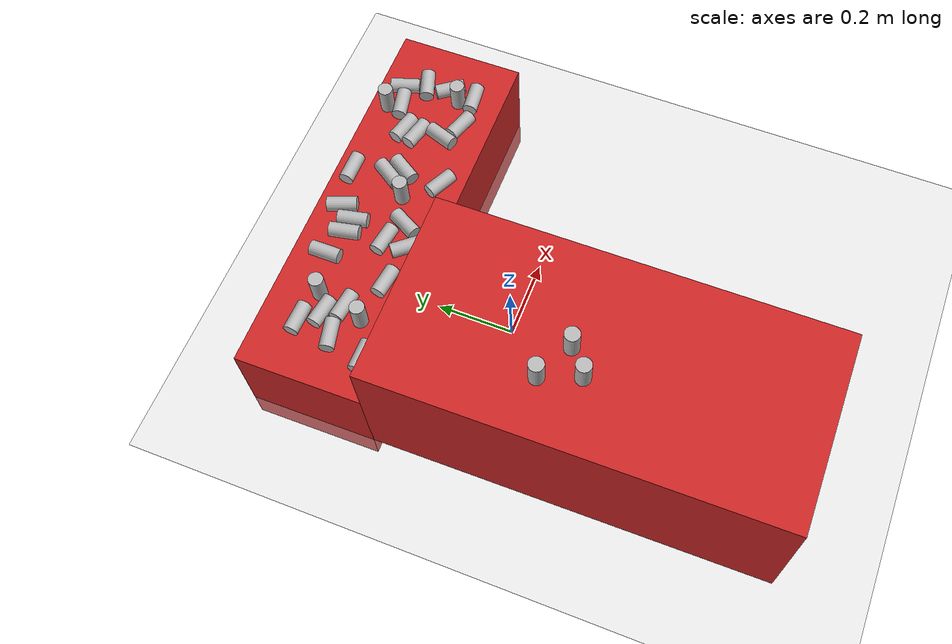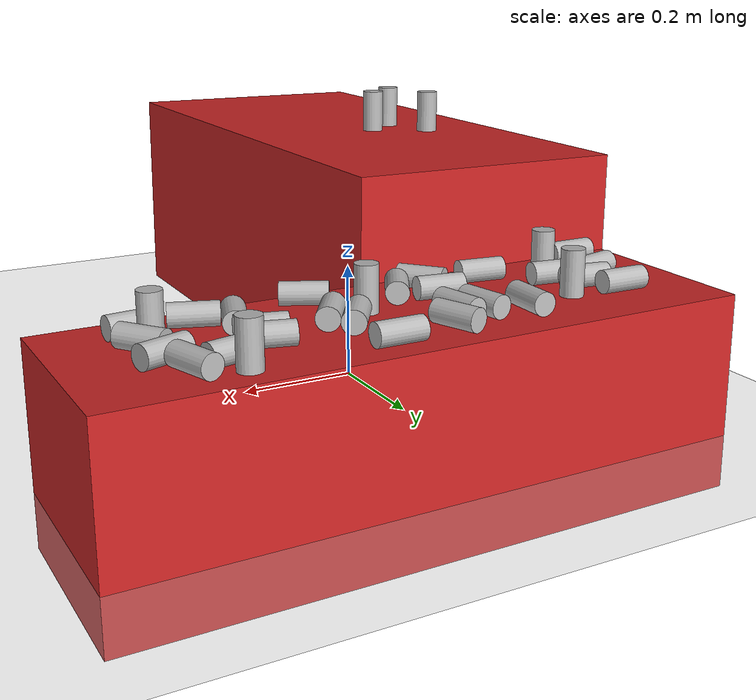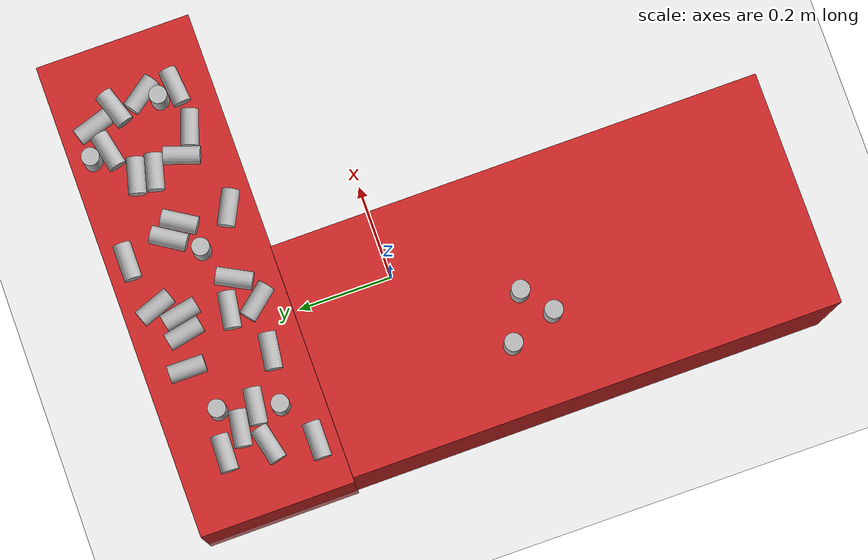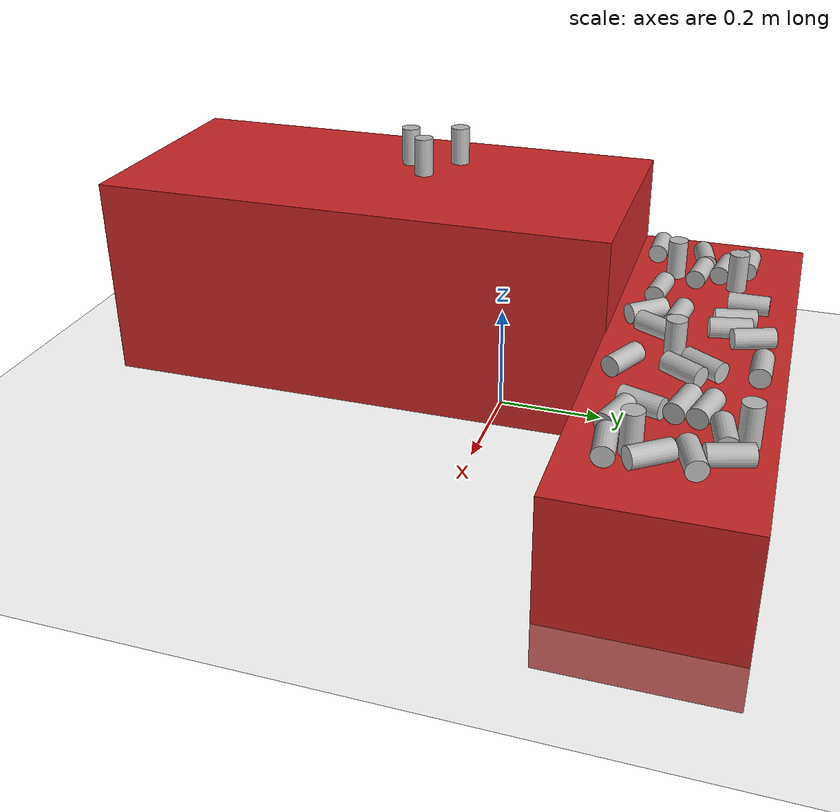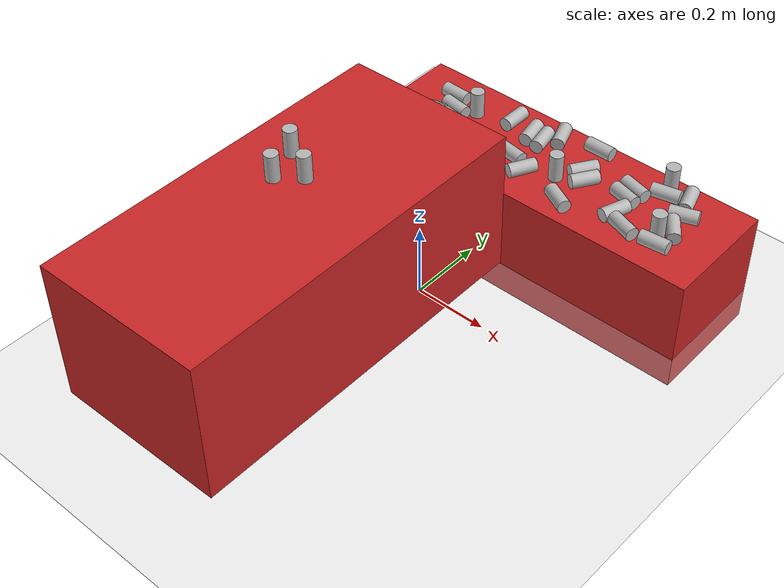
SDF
<sdf version="1.7">
 <world name="default">
  <light name="sun" type="directional">
   <pose>0 0 10 0 -0 0</pose>
   <diffuse>0.8 0.8 0.8 1</diffuse>
   <specular>0.2 0.2 0.2 1</specular>
   <attenuation>
    <range>1000</range>
    <constant>0.9</constant>
    <linear>0.01</linear>
    <quadratic>0.001</quadratic>
   </attenuation>
   <direction>-0.5 0.1 -0.9</direction>
   <spot><inner_angle>0</inner_angle><outer_angle>0</outer_angle><falloff>0</falloff></spot>
  </light>
  <model name="ground_plane">
   <static>1</static>
   <link name="link">
    <collision name="collision">
     <geometry><plane><normal>0 0 1</normal><size>100 100</size></plane></geometry>
     <surface>
      <contact><collide_bitmask>65535</collide_bitmask></contact>
      <friction><ode><mu>100</mu><mu2>50</mu2></ode></friction>
     </surface>
    </collision>
    <visual name="visual">
     <cast_shadows>0</cast_shadows>
     <geometry><plane><normal>0 0 1</normal><size>100 100</size></plane></geometry>
     <material>
      <script><uri>file://media/materials/scripts/gazebo.material</uri><name>Gazebo/Grey</name></script>
     </material>
    </visual>
   </link>
  </model>
  <gravity>0 0 -9.8</gravity>
  <magnetic_field>6e-06 2.3e-05 -4.2e-05</magnetic_field>
  <atmosphere type="adiabatic"/>
  <physics type="ode">
   <max_step_size>0.001</max_step_size>
   <real_time_factor>1</real_time_factor>
   <real_time_update_rate>1000</real_time_update_rate>
  </physics>
  <scene><ambient>0.4 0.4 0.4 1</ambient><background>0.7 0.7 0.7 1</background><shadows>1</shadows></scene>
  <spherical_coordinates>
   <surface_model>EARTH_WGS84</surface_model>
   <latitude_deg>0</latitude_deg>
   <longitude_deg>0</longitude_deg>
   <elevation>0</elevation>
   <heading_deg>0</heading_deg>
  </spherical_coordinates>
  <model name="robot_station">
   <static>1</static>
   <link name="link">
    <inertial>
     <mass>100</mass>
     <inertia>
      <ixx>0.166667</ixx>
      <ixy>0</ixy>
      <ixz>0</ixz>
      <iyy>0.166667</iyy>
      <iyz>0</iyz>
      <izz>0.166667</izz>
     </inertia>
    </inertial>
    <visual name="visual">
     <geometry><box><size>0.477763 1.00606 0.398553</size></box></geometry>
     <material>
      <script><name>Gazebo/Red</name><uri>file://media/materials/scripts/gazebo.material</uri></script>
      <shader type="pixel"/>
     </material>
    </visual>
    <collision name="collision">
     <geometry><box><size>0.477763 1.00606 0.398553</size></box></geometry>
     <surface>
      <friction>
       <ode><mu>1</mu><mu2>1</mu2><fdir1>0 0 0</fdir1><slip1>0</slip1><slip2>0</slip2></ode>
       <torsional>
        <coefficient>1</coefficient>
        <patch_radius>0</patch_radius>
        <surface_radius>0</surface_radius>
        <use_patch_radius>1</use_patch_radius>
        <ode><slip>0</slip></ode>
       </torsional>
      </friction>
      <bounce><restitution_coefficient>0</restitution_coefficient><threshold>1e+06</threshold></bounce>
      <contact>
       <collide_without_contact>0</collide_without_contact>
       <collide_without_contact_bitmask>1</collide_without_contact_bitmask>
       <collide_bitmask>1</collide_bitmask>
       <ode>
        <soft_cfm>0</soft_cfm>
        <soft_erp>0.2</soft_erp>
        <kp>1e+13</kp>
        <kd>1</kd>
        <max_vel>0.01</max_vel>
        <min_depth>0</min_depth>
       </ode>
       <bullet>
        <split_impulse>1</split_impulse>
        <split_impulse_penetration_threshold>-0.01</split_impulse_penetration_threshold>
        <soft_cfm>0</soft_cfm>
        <soft_erp>0.2</soft_erp>
        <kp>1e+13</kp>
        <kd>1</kd>
       </bullet>
      </contact>
     </surface>
    </collision>
   </link>
   <pose>-0.148839 -0.291094 0.199608 -1e-06 -0.011075 0.008285</pose>
  </model>
  <model name="robot_station_clone">
   <static>1</static>
   <link name="link">
    <inertial>
     <mass>100</mass>
     <inertia>
      <ixx>0.166667</ixx>
      <ixy>0</ixy>
      <ixz>0</ixz>
      <iyy>0.166667</iyy>
      <iyz>0</iyz>
      <izz>0.166667</izz>
     </inertia>
    </inertial>
    <visual name="visual">
     <geometry><box><size>1.00072 0.323595 0.318232</size></box></geometry>
     <material>
      <script><name>Gazebo/Red</name><uri>file://media/materials/scripts/gazebo.material</uri></script>
      <shader type="pixel"/>
     </material>
    </visual>
    <collision name="collision">
     <geometry><box><size>1.00072 0.323595 0.318232</size></box></geometry>
     <surface>
      <friction>
       <ode><mu>1</mu><mu2>1</mu2><fdir1>0 0 0</fdir1><slip1>0</slip1><slip2>0</slip2></ode>
       <torsional>
        <coefficient>1</coefficient>
        <patch_radius>0</patch_radius>
        <surface_radius>0</surface_radius>
        <use_patch_radius>1</use_patch_radius>
        <ode><slip>0</slip></ode>
       </torsional>
      </friction>
      <bounce><restitution_coefficient>0</restitution_coefficient><threshold>1e+06</threshold></bounce>
      <contact>
       <collide_without_contact>0</collide_without_contact>
       <collide_without_contact_bitmask>1</collide_without_contact_bitmask>
       <collide_bitmask>1</collide_bitmask>
       <ode>
        <soft_cfm>0</soft_cfm>
        <soft_erp>0.2</soft_erp>
        <kp>1e+13</kp>
        <kd>1</kd>
        <max_vel>0.01</max_vel>
        <min_depth>0</min_depth>
       </ode>
       <bullet>
        <split_impulse>1</split_impulse>
        <split_impulse_penetration_threshold>-0.01</split_impulse_penetration_threshold>
        <soft_cfm>0</soft_cfm>
        <soft_erp>0.2</soft_erp>
        <kp>1e+13</kp>
        <kd>1</kd>
       </bullet>
      </contact>
     </surface>
    </collision>
   </link>
   <pose>0.108828 0.374252 0.07048 -1e-06 0.000369 0.008285</pose>
  </model>
  <model name="sprite">
   <link name="link_0">
    <inertial>
     <mass>0.00147636</mass>
     <inertia>
      <ixx>4.89601e-06</ixx>
      <ixy>0</ixy>
      <ixz>0</ixz>
      <iyy>4.89601e-06</iyy>
      <iyz>0</iyz>
      <izz>1.48331e-06</izz>
     </inertia>
    </inertial>
    <visual name="visual">
     <geometry><cylinder><radius>0.018402</radius><length>0.074444</length></cylinder></geometry>
     <material>
      <lighting>1</lighting>
      <script>
       <uri>model://sprite/materials/scripts</uri>
       <uri>model://sprite/materials/textures</uri>
       <name>sprite</name>
      </script>
      <shader type="pixel"/>
     </material>
    </visual>
    <collision name="collision">
     <geometry><cylinder><radius>0.018402</radius><length>0.074444</length></cylinder></geometry>
     <surface>
      <friction>
       <ode><mu>1</mu><mu2>1</mu2><fdir1>0 0 0</fdir1><slip1>0</slip1><slip2>0</slip2></ode>
       <torsional>
        <coefficient>1</coefficient>
        <patch_radius>0</patch_radius>
        <surface_radius>0</surface_radius>
        <use_patch_radius>1</use_patch_radius>
        <ode><slip>0</slip></ode>
       </torsional>
      </friction>
      <bounce><restitution_coefficient>0</restitution_coefficient><threshold>1e+06</threshold></bounce>
      <contact>
       <collide_without_contact>0</collide_without_contact>
       <collide_without_contact_bitmask>1</collide_without_contact_bitmask>
       <collide_bitmask>1</collide_bitmask>
       <ode>
        <soft_cfm>0</soft_cfm>
        <soft_erp>0.2</soft_erp>
        <kp>1e+13</kp>
        <kd>1</kd>
        <max_vel>0.01</max_vel>
        <min_depth>0</min_depth>
       </ode>
       <bullet>
        <split_impulse>1</split_impulse>
        <split_impulse_penetration_threshold>-0.01</split_impulse_penetration_threshold>
        <soft_cfm>0</soft_cfm>
        <soft_erp>0.2</soft_erp>
        <kp>1e+13</kp>
        <kd>1</kd>
       </bullet>
      </contact>
     </surface>
    </collision>
   </link>
   <static>0</static>
   <pose>-0.221494 -0.259296 0.435314 0.000233 -0.011327 -0.004647</pose>
  </model>
  <model name="pepsi_0">
   <link name="link_0">
    <inertial>
     <mass>0.00147636</mass>
     <inertia>
      <ixx>4.89601e-06</ixx>
      <ixy>0</ixy>
      <ixz>0</ixz>
      <iyy>4.89601e-06</iyy>
      <iyz>0</iyz>
      <izz>1.48331e-06</izz>
     </inertia>
    </inertial>
    <visual name="visual">
     <geometry><cylinder><radius>0.018402</radius><length>0.074444</length></cylinder></geometry>
     <material>
      <lighting>1</lighting>
      <script>
       <uri>model://pepsi/materials/scripts</uri>
       <uri>model://pepsi/materials/textures</uri>
       <name>pepsi</name>
      </script>
      <shader type="pixel"/>
     </material>
    </visual>
    <collision name="collision">
     <geometry><cylinder><radius>0.018402</radius><length>0.074444</length></cylinder></geometry>
     <surface>
      <friction>
       <ode><mu>1</mu><mu2>1</mu2><fdir1>0 0 0</fdir1><slip1>0</slip1><slip2>0</slip2></ode>
       <torsional>
        <coefficient>1</coefficient>
        <patch_radius>0</patch_radius>
        <surface_radius>0</surface_radius>
        <use_patch_radius>1</use_patch_radius>
        <ode><slip>0</slip></ode>
       </torsional>
      </friction>
      <bounce><restitution_coefficient>0</restitution_coefficient><threshold>1e+06</threshold></bounce>
      <contact>
       <collide_without_contact>0</collide_without_contact>
       <collide_without_contact_bitmask>1</collide_without_contact_bitmask>
       <collide_bitmask>1</collide_bitmask>
       <ode>
        <soft_cfm>0</soft_cfm>
        <soft_erp>0.2</soft_erp>
        <kp>1e+13</kp>
        <kd>1</kd>
        <max_vel>0.01</max_vel>
        <min_depth>0</min_depth>
       </ode>
       <bullet>
        <split_impulse>1</split_impulse>
        <split_impulse_penetration_threshold>-0.01</split_impulse_penetration_threshold>
        <soft_cfm>0</soft_cfm>
        <soft_erp>0.2</soft_erp>
        <kp>1e+13</kp>
        <kd>1</kd>
       </bullet>
      </contact>
     </surface>
    </collision>
   </link>
   <static>0</static>
   <pose>-0.163639 -0.212135 0.435959 0.000239 -0.01133 -0.006572</pose>
  </model>
  <model name="coke_0">
   <link name="link_0">
    <inertial>
     <mass>0.00147636</mass>
     <inertia>
      <ixx>4.89601e-06</ixx>
      <ixy>0</ixy>
      <ixz>0</ixz>
      <iyy>4.89601e-06</iyy>
      <iyz>0</iyz>
      <izz>1.48331e-06</izz>
     </inertia>
    </inertial>
    <visual name="visual">
     <geometry><cylinder><radius>0.018402</radius><length>0.074444</length></cylinder></geometry>
     <material>
      <lighting>1</lighting>
      <script>
       <uri>model://coke/materials/scripts</uri>
       <uri>model://coke/materials/textures</uri>
       <name>coke</name>
      </script>
      <shader type="pixel"/>
     </material>
    </visual>
    <collision name="collision">
     <geometry><cylinder><radius>0.018402</radius><length>0.074444</length></cylinder></geometry>
     <surface>
      <friction>
       <ode><mu>1</mu><mu2>1</mu2><fdir1>0 0 0</fdir1><slip1>0</slip1><slip2>0</slip2></ode>
       <torsional>
        <coefficient>1</coefficient>
        <patch_radius>0</patch_radius>
        <surface_radius>0</surface_radius>
        <use_patch_radius>1</use_patch_radius>
        <ode><slip>0</slip></ode>
       </torsional>
      </friction>
      <bounce><restitution_coefficient>0</restitution_coefficient><threshold>1e+06</threshold></bounce>
      <contact>
       <collide_without_contact>0</collide_without_contact>
       <collide_without_contact_bitmask>1</collide_without_contact_bitmask>
       <collide_bitmask>1</collide_bitmask>
       <ode>
        <soft_cfm>0</soft_cfm>
        <soft_erp>0.2</soft_erp>
        <kp>1e+13</kp>
        <kd>1</kd>
        <max_vel>0.01</max_vel>
        <min_depth>0</min_depth>
       </ode>
       <bullet>
        <split_impulse>1</split_impulse>
        <split_impulse_penetration_threshold>-0.01</split_impulse_penetration_threshold>
        <soft_cfm>0</soft_cfm>
        <soft_erp>0.2</soft_erp>
        <kp>1e+13</kp>
        <kd>1</kd>
       </bullet>
      </contact>
     </surface>
    </collision>
   </link>
   <static>0</static>
   <pose>-0.255563 -0.16538 0.434945 0.000315 -0.011288 -0.012086</pose>
  </model>
  <model name="obj_s_1">
   <link name="link_0">
    <inertial>
     <mass>0.00147636</mass>
     <inertia>
      <ixx>4.89601e-06</ixx>
      <ixy>0</ixy>
      <ixz>0</ixz>
      <iyy>4.89601e-06</iyy>
      <iyz>0</iyz>
      <izz>1.48331e-06</izz>
     </inertia>
    </inertial>
    <visual name="visual">
     <geometry><cylinder><radius>0.018402</radius><length>0.074444</length></cylinder></geometry>
     <material>
      <lighting>1</lighting>
      <script>
       <uri>model://sprite/materials/scripts</uri>
       <uri>model://sprite/materials/textures</uri>
       <name>sprite</name>
      </script>
      <shader type="pixel"/>
     </material>
    </visual>
    <collision name="collision">
     <geometry><cylinder><radius>0.018402</radius><length>0.074444</length></cylinder></geometry>
     <surface>
      <friction>
       <ode><mu>1</mu><mu2>1</mu2><fdir1>0 0 0</fdir1><slip1>0</slip1><slip2>0</slip2></ode>
       <torsional>
        <coefficient>1</coefficient>
        <patch_radius>0</patch_radius>
        <surface_radius>0</surface_radius>
        <use_patch_radius>1</use_patch_radius>
        <ode><slip>0</slip></ode>
       </torsional>
      </friction>
      <bounce><restitution_coefficient>0</restitution_coefficient><threshold>1e+06</threshold></bounce>
      <contact>
       <collide_without_contact>0</collide_without_contact>
       <collide_without_contact_bitmask>1</collide_without_contact_bitmask>
       <collide_bitmask>1</collide_bitmask>
       <ode>
        <soft_cfm>0</soft_cfm>
        <soft_erp>0.2</soft_erp>
        <kp>1e+13</kp>
        <kd>1</kd>
        <max_vel>0.01</max_vel>
        <min_depth>0</min_depth>
       </ode>
       <bullet>
        <split_impulse>1</split_impulse>
        <split_impulse_penetration_threshold>-0.01</split_impulse_penetration_threshold>
        <soft_cfm>0</soft_cfm>
        <soft_erp>0.2</soft_erp>
        <kp>1e+13</kp>
        <kd>1</kd>
       </bullet>
      </contact>
     </surface>
    </collision>
   </link>
   <static>0</static>
   <pose>-0.2646 0.345325 0.249047 1.57073 -0.952484 -1.3369</pose>
  </model>
  <model name="obj_s_2">
   <link name="link_0">
    <inertial>
     <mass>0.00147636</mass>
     <inertia>
      <ixx>4.89601e-06</ixx>
      <ixy>0</ixy>
      <ixz>0</ixz>
      <iyy>4.89601e-06</iyy>
      <iyz>0</iyz>
      <izz>1.48331e-06</izz>
     </inertia>
    </inertial>
    <visual name="visual">
     <geometry><cylinder><radius>0.018402</radius><length>0.074444</length></cylinder></geometry>
     <material>
      <lighting>1</lighting>
      <script>
       <uri>model://sprite/materials/scripts</uri>
       <uri>model://sprite/materials/textures</uri>
       <name>sprite</name>
      </script>
      <shader type="pixel"/>
     </material>
    </visual>
    <collision name="collision">
     <geometry><cylinder><radius>0.018402</radius><length>0.074444</length></cylinder></geometry>
     <surface>
      <friction>
       <ode><mu>1</mu><mu2>1</mu2><fdir1>0 0 0</fdir1><slip1>0</slip1><slip2>0</slip2></ode>
       <torsional>
        <coefficient>1</coefficient>
        <patch_radius>0</patch_radius>
        <surface_radius>0</surface_radius>
        <use_patch_radius>1</use_patch_radius>
        <ode><slip>0</slip></ode>
       </torsional>
      </friction>
      <bounce><restitution_coefficient>0</restitution_coefficient><threshold>1e+06</threshold></bounce>
      <contact>
       <collide_without_contact>0</collide_without_contact>
       <collide_without_contact_bitmask>1</collide_without_contact_bitmask>
       <collide_bitmask>1</collide_bitmask>
       <ode>
        <soft_cfm>0</soft_cfm>
        <soft_erp>0.2</soft_erp>
        <kp>1e+13</kp>
        <kd>1</kd>
        <max_vel>0.01</max_vel>
        <min_depth>0</min_depth>
       </ode>
       <bullet>
        <split_impulse>1</split_impulse>
        <split_impulse_penetration_threshold>-0.01</split_impulse_penetration_threshold>
        <soft_cfm>0</soft_cfm>
        <soft_erp>0.2</soft_erp>
        <kp>1e+13</kp>
        <kd>1</kd>
       </bullet>
      </contact>
     </surface>
    </collision>
   </link>
   <static>0</static>
   <pose>-0.200771 0.297373 0.267882 0.000128 -0.000285 -0.315537</pose>
  </model>
  <model name="obj_s_3">
   <link name="link_0">
    <inertial>
     <mass>0.00147636</mass>
     <inertia>
      <ixx>4.89601e-06</ixx>
      <ixy>0</ixy>
      <ixz>0</ixz>
      <iyy>4.89601e-06</iyy>
      <iyz>0</iyz>
      <izz>1.48331e-06</izz>
     </inertia>
    </inertial>
    <visual name="visual">
     <geometry><cylinder><radius>0.018402</radius><length>0.074444</length></cylinder></geometry>
     <material>
      <lighting>1</lighting>
      <script>
       <uri>model://sprite/materials/scripts</uri>
       <uri>model://sprite/materials/textures</uri>
       <name>sprite</name>
      </script>
      <shader type="pixel"/>
     </material>
    </visual>
    <collision name="collision">
     <geometry><cylinder><radius>0.018402</radius><length>0.074444</length></cylinder></geometry>
     <surface>
      <friction>
       <ode><mu>1</mu><mu2>1</mu2><fdir1>0 0 0</fdir1><slip1>0</slip1><slip2>0</slip2></ode>
       <torsional>
        <coefficient>1</coefficient>
        <patch_radius>0</patch_radius>
        <surface_radius>0</surface_radius>
        <use_patch_radius>1</use_patch_radius>
        <ode><slip>0</slip></ode>
       </torsional>
      </friction>
      <bounce><restitution_coefficient>0</restitution_coefficient><threshold>1e+06</threshold></bounce>
      <contact>
       <collide_without_contact>0</collide_without_contact>
       <collide_without_contact_bitmask>1</collide_without_contact_bitmask>
       <collide_bitmask>1</collide_bitmask>
       <ode>
        <soft_cfm>0</soft_cfm>
        <soft_erp>0.2</soft_erp>
        <kp>1e+13</kp>
        <kd>1</kd>
        <max_vel>0.01</max_vel>
        <min_depth>0</min_depth>
       </ode>
       <bullet>
        <split_impulse>1</split_impulse>
        <split_impulse_penetration_threshold>-0.01</split_impulse_penetration_threshold>
        <soft_cfm>0</soft_cfm>
        <soft_erp>0.2</soft_erp>
        <kp>1e+13</kp>
        <kd>1</kd>
       </bullet>
      </contact>
     </surface>
    </collision>
   </link>
   <static>0</static>
   <pose>-0.090618 0.282021 0.249046 -1.57081 -0.645072 -1.69907</pose>
  </model>
  <model name="obj_s_4">
   <link name="link_0">
    <inertial>
     <mass>0.00147636</mass>
     <inertia>
      <ixx>4.89601e-06</ixx>
      <ixy>0</ixy>
      <ixz>0</ixz>
      <iyy>4.89601e-06</iyy>
      <iyz>0</iyz>
      <izz>1.48331e-06</izz>
     </inertia>
    </inertial>
    <visual name="visual">
     <geometry><cylinder><radius>0.018402</radius><length>0.074444</length></cylinder></geometry>
     <material>
      <lighting>1</lighting>
      <script>
       <uri>model://sprite/materials/scripts</uri>
       <uri>model://sprite/materials/textures</uri>
       <name>sprite</name>
      </script>
      <shader type="pixel"/>
     </material>
    </visual>
    <collision name="collision">
     <geometry><cylinder><radius>0.018402</radius><length>0.074444</length></cylinder></geometry>
     <surface>
      <friction>
       <ode><mu>1</mu><mu2>1</mu2><fdir1>0 0 0</fdir1><slip1>0</slip1><slip2>0</slip2></ode>
       <torsional>
        <coefficient>1</coefficient>
        <patch_radius>0</patch_radius>
        <surface_radius>0</surface_radius>
        <use_patch_radius>1</use_patch_radius>
        <ode><slip>0</slip></ode>
       </torsional>
      </friction>
      <bounce><restitution_coefficient>0</restitution_coefficient><threshold>1e+06</threshold></bounce>
      <contact>
       <collide_without_contact>0</collide_without_contact>
       <collide_without_contact_bitmask>1</collide_without_contact_bitmask>
       <collide_bitmask>1</collide_bitmask>
       <ode>
        <soft_cfm>0</soft_cfm>
        <soft_erp>0.2</soft_erp>
        <kp>1e+13</kp>
        <kd>1</kd>
        <max_vel>0.01</max_vel>
        <min_depth>0</min_depth>
       </ode>
       <bullet>
        <split_impulse>1</split_impulse>
        <split_impulse_penetration_threshold>-0.01</split_impulse_penetration_threshold>
        <soft_cfm>0</soft_cfm>
        <soft_erp>0.2</soft_erp>
        <kp>1e+13</kp>
        <kd>1</kd>
       </bullet>
      </contact>
     </surface>
    </collision>
   </link>
   <static>0</static>
   <pose>-0.069769 0.448923 0.249056 -1.5708 -0.578227 0.000529</pose>
  </model>
  <model name="obj_s_5">
   <link name="link_0">
    <inertial>
     <mass>0.00147636</mass>
     <inertia>
      <ixx>4.89601e-06</ixx>
      <ixy>0</ixy>
      <ixz>0</ixz>
      <iyy>4.89601e-06</iyy>
      <iyz>0</iyz>
      <izz>1.48331e-06</izz>
     </inertia>
    </inertial>
    <visual name="visual">
     <geometry><cylinder><radius>0.018402</radius><length>0.074444</length></cylinder></geometry>
     <material>
      <lighting>1</lighting>
      <script>
       <uri>model://sprite/materials/scripts</uri>
       <uri>model://sprite/materials/textures</uri>
       <name>sprite</name>
      </script>
      <shader type="pixel"/>
     </material>
    </visual>
    <collision name="collision">
     <geometry><cylinder><radius>0.018402</radius><length>0.074444</length></cylinder></geometry>
     <surface>
      <friction>
       <ode><mu>1</mu><mu2>1</mu2><fdir1>0 0 0</fdir1><slip1>0</slip1><slip2>0</slip2></ode>
       <torsional>
        <coefficient>1</coefficient>
        <patch_radius>0</patch_radius>
        <surface_radius>0</surface_radius>
        <use_patch_radius>1</use_patch_radius>
        <ode><slip>0</slip></ode>
       </torsional>
      </friction>
      <bounce><restitution_coefficient>0</restitution_coefficient><threshold>1e+06</threshold></bounce>
      <contact>
       <collide_without_contact>0</collide_without_contact>
       <collide_without_contact_bitmask>1</collide_without_contact_bitmask>
       <collide_bitmask>1</collide_bitmask>
       <ode>
        <soft_cfm>0</soft_cfm>
        <soft_erp>0.2</soft_erp>
        <kp>1e+13</kp>
        <kd>1</kd>
        <max_vel>0.01</max_vel>
        <min_depth>0</min_depth>
       </ode>
       <bullet>
        <split_impulse>1</split_impulse>
        <split_impulse_penetration_threshold>-0.01</split_impulse_penetration_threshold>
        <soft_cfm>0</soft_cfm>
        <soft_erp>0.2</soft_erp>
        <kp>1e+13</kp>
        <kd>1</kd>
       </bullet>
      </contact>
     </surface>
    </collision>
   </link>
   <static>0</static>
   <pose>-0.288337 0.25268 0.249048 1.57073 0.870032 -1.57085</pose>
  </model>
  <model name="obj_s_0">
   <link name="link_0">
    <inertial>
     <mass>0.00147636</mass>
     <inertia>
      <ixx>4.89601e-06</ixx>
      <ixy>0</ixy>
      <ixz>0</ixz>
      <iyy>4.89601e-06</iyy>
      <iyz>0</iyz>
      <izz>1.48331e-06</izz>
     </inertia>
    </inertial>
    <visual name="visual">
     <geometry><cylinder><radius>0.018402</radius><length>0.074444</length></cylinder></geometry>
     <material>
      <lighting>1</lighting>
      <script>
       <uri>model://sprite/materials/scripts</uri>
       <uri>model://sprite/materials/textures</uri>
       <name>sprite</name>
      </script>
      <shader type="pixel"/>
     </material>
    </visual>
    <collision name="collision">
     <geometry><cylinder><radius>0.018402</radius><length>0.074444</length></cylinder></geometry>
     <surface>
      <friction>
       <ode><mu>1</mu><mu2>1</mu2><fdir1>0 0 0</fdir1><slip1>0</slip1><slip2>0</slip2></ode>
       <torsional>
        <coefficient>1</coefficient>
        <patch_radius>0</patch_radius>
        <surface_radius>0</surface_radius>
        <use_patch_radius>1</use_patch_radius>
        <ode><slip>0</slip></ode>
       </torsional>
      </friction>
      <bounce><restitution_coefficient>0</restitution_coefficient><threshold>1e+06</threshold></bounce>
      <contact>
       <collide_without_contact>0</collide_without_contact>
       <collide_without_contact_bitmask>1</collide_without_contact_bitmask>
       <collide_bitmask>1</collide_bitmask>
       <ode>
        <soft_cfm>0</soft_cfm>
        <soft_erp>0.2</soft_erp>
        <kp>1e+13</kp>
        <kd>1</kd>
        <max_vel>0.01</max_vel>
        <min_depth>0</min_depth>
       </ode>
       <bullet>
        <split_impulse>1</split_impulse>
        <split_impulse_penetration_threshold>-0.01</split_impulse_penetration_threshold>
        <soft_cfm>0</soft_cfm>
        <soft_erp>0.2</soft_erp>
        <kp>1e+13</kp>
        <kd>1</kd>
       </bullet>
      </contact>
     </surface>
    </collision>
   </link>
   <static>0</static>
   <pose>-0.169124 0.41751 0.267872 0.000107 -0.000268 0.156933</pose>
  </model>
  <model name="obj_s_6">
   <link name="link_0">
    <inertial>
     <mass>0.00147636</mass>
     <inertia>
      <ixx>4.89601e-06</ixx>
      <ixy>0</ixy>
      <ixz>0</ixz>
      <iyy>4.89601e-06</iyy>
      <iyz>0</iyz>
      <izz>1.48331e-06</izz>
     </inertia>
    </inertial>
    <visual name="visual">
     <geometry><cylinder><radius>0.018402</radius><length>0.074444</length></cylinder></geometry>
     <material>
      <lighting>1</lighting>
      <script>
       <uri>model://sprite/materials/scripts</uri>
       <uri>model://sprite/materials/textures</uri>
       <name>sprite</name>
      </script>
      <shader type="pixel"/>
     </material>
    </visual>
    <collision name="collision">
     <geometry><cylinder><radius>0.018402</radius><length>0.074444</length></cylinder></geometry>
     <surface>
      <friction>
       <ode><mu>1</mu><mu2>1</mu2><fdir1>0 0 0</fdir1><slip1>0</slip1><slip2>0</slip2></ode>
       <torsional>
        <coefficient>1</coefficient>
        <patch_radius>0</patch_radius>
        <surface_radius>0</surface_radius>
        <use_patch_radius>1</use_patch_radius>
        <ode><slip>0</slip></ode>
       </torsional>
      </friction>
      <bounce><restitution_coefficient>0</restitution_coefficient><threshold>1e+06</threshold></bounce>
      <contact>
       <collide_without_contact>0</collide_without_contact>
       <collide_without_contact_bitmask>1</collide_without_contact_bitmask>
       <collide_bitmask>1</collide_bitmask>
       <ode>
        <soft_cfm>0</soft_cfm>
        <soft_erp>0.2</soft_erp>
        <kp>1e+13</kp>
        <kd>1</kd>
        <max_vel>0.01</max_vel>
        <min_depth>0</min_depth>
       </ode>
       <bullet>
        <split_impulse>1</split_impulse>
        <split_impulse_penetration_threshold>-0.01</split_impulse_penetration_threshold>
        <soft_cfm>0</soft_cfm>
        <soft_erp>0.2</soft_erp>
        <kp>1e+13</kp>
        <kd>1</kd>
       </bullet>
      </contact>
     </surface>
    </collision>
   </link>
   <static>0</static>
   <pose>-0.216381 0.388058 0.249056 -1.5708 1.12455 -1.71783</pose>
  </model>
  <model name="obj_s_8">
   <link name="link_0">
    <inertial>
     <mass>0.00147636</mass>
     <inertia>
      <ixx>4.89601e-06</ixx>
      <ixy>0</ixy>
      <ixz>0</ixz>
      <iyy>4.89601e-06</iyy>
      <iyz>0</iyz>
      <izz>1.48331e-06</izz>
     </inertia>
    </inertial>
    <visual name="visual">
     <geometry><cylinder><radius>0.018402</radius><length>0.074444</length></cylinder></geometry>
     <material>
      <lighting>1</lighting>
      <script>
       <uri>model://sprite/materials/scripts</uri>
       <uri>model://sprite/materials/textures</uri>
       <name>sprite</name>
      </script>
      <shader type="pixel"/>
     </material>
    </visual>
    <collision name="collision">
     <geometry><cylinder><radius>0.018402</radius><length>0.074444</length></cylinder></geometry>
     <surface>
      <friction>
       <ode><mu>1</mu><mu2>1</mu2><fdir1>0 0 0</fdir1><slip1>0</slip1><slip2>0</slip2></ode>
       <torsional>
        <coefficient>1</coefficient>
        <patch_radius>0</patch_radius>
        <surface_radius>0</surface_radius>
        <use_patch_radius>1</use_patch_radius>
        <ode><slip>0</slip></ode>
       </torsional>
      </friction>
      <bounce><restitution_coefficient>0</restitution_coefficient><threshold>1e+06</threshold></bounce>
      <contact>
       <collide_without_contact>0</collide_without_contact>
       <collide_without_contact_bitmask>1</collide_without_contact_bitmask>
       <collide_bitmask>1</collide_bitmask>
       <ode>
        <soft_cfm>0</soft_cfm>
        <soft_erp>0.2</soft_erp>
        <kp>1e+13</kp>
        <kd>1</kd>
        <max_vel>0.01</max_vel>
        <min_depth>0</min_depth>
       </ode>
       <bullet>
        <split_impulse>1</split_impulse>
        <split_impulse_penetration_threshold>-0.01</split_impulse_penetration_threshold>
        <soft_cfm>0</soft_cfm>
        <soft_erp>0.2</soft_erp>
        <kp>1e+13</kp>
        <kd>1</kd>
       </bullet>
      </contact>
     </surface>
    </collision>
   </link>
   <static>0</static>
   <pose>-0.184685 0.345709 0.249055 -1.57074 0.864661 -1.69952</pose>
  </model>
  <model name="obj_s_10">
   <link name="link_0">
    <inertial>
     <mass>0.00147636</mass>
     <inertia>
      <ixx>4.89601e-06</ixx>
      <ixy>0</ixy>
      <ixz>0</ixz>
      <iyy>4.89601e-06</iyy>
      <iyz>0</iyz>
      <izz>1.48331e-06</izz>
     </inertia>
    </inertial>
    <visual name="visual">
     <geometry><cylinder><radius>0.018402</radius><length>0.074444</length></cylinder></geometry>
     <material>
      <lighting>1</lighting>
      <script>
       <uri>model://sprite/materials/scripts</uri>
       <uri>model://sprite/materials/textures</uri>
       <name>sprite</name>
      </script>
      <shader type="pixel"/>
     </material>
    </visual>
    <collision name="collision">
     <geometry><cylinder><radius>0.018402</radius><length>0.074444</length></cylinder></geometry>
     <surface>
      <friction>
       <ode><mu>1</mu><mu2>1</mu2><fdir1>0 0 0</fdir1><slip1>0</slip1><slip2>0</slip2></ode>
       <torsional>
        <coefficient>1</coefficient>
        <patch_radius>0</patch_radius>
        <surface_radius>0</surface_radius>
        <use_patch_radius>1</use_patch_radius>
        <ode><slip>0</slip></ode>
       </torsional>
      </friction>
      <bounce><restitution_coefficient>0</restitution_coefficient><threshold>1e+06</threshold></bounce>
      <contact>
       <collide_without_contact>0</collide_without_contact>
       <collide_without_contact_bitmask>1</collide_without_contact_bitmask>
       <collide_bitmask>1</collide_bitmask>
       <ode>
        <soft_cfm>0</soft_cfm>
        <soft_erp>0.2</soft_erp>
        <kp>1e+13</kp>
        <kd>1</kd>
        <max_vel>0.01</max_vel>
        <min_depth>0</min_depth>
       </ode>
       <bullet>
        <split_impulse>1</split_impulse>
        <split_impulse_penetration_threshold>-0.01</split_impulse_penetration_threshold>
        <soft_cfm>0</soft_cfm>
        <soft_erp>0.2</soft_erp>
        <kp>1e+13</kp>
        <kd>1</kd>
       </bullet>
      </contact>
     </surface>
    </collision>
   </link>
   <static>0</static>
   <pose>-0.252392 0.433081 0.249047 1.57096 1.38475 -1.59848</pose>
  </model>
  <model name="obj_p_0">
   <link name="link_0">
    <inertial>
     <mass>0.00147636</mass>
     <inertia>
      <ixx>4.89601e-06</ixx>
      <ixy>0</ixy>
      <ixz>0</ixz>
      <iyy>4.89601e-06</iyy>
      <iyz>0</iyz>
      <izz>1.48331e-06</izz>
     </inertia>
    </inertial>
    <visual name="visual">
     <geometry><cylinder><radius>0.018402</radius><length>0.074444</length></cylinder></geometry>
     <material>
      <lighting>1</lighting>
      <script>
       <uri>model://pepsi/materials/scripts</uri>
       <uri>model://pepsi/materials/textures</uri>
       <name>pepsi</name>
      </script>
      <shader type="pixel"/>
     </material>
    </visual>
    <collision name="collision">
     <geometry><cylinder><radius>0.018402</radius><length>0.074444</length></cylinder></geometry>
     <surface>
      <friction>
       <ode><mu>1</mu><mu2>1</mu2><fdir1>0 0 0</fdir1><slip1>0</slip1><slip2>0</slip2></ode>
       <torsional>
        <coefficient>1</coefficient>
        <patch_radius>0</patch_radius>
        <surface_radius>0</surface_radius>
        <use_patch_radius>1</use_patch_radius>
        <ode><slip>0</slip></ode>
       </torsional>
      </friction>
      <bounce><restitution_coefficient>0</restitution_coefficient><threshold>1e+06</threshold></bounce>
      <contact>
       <collide_without_contact>0</collide_without_contact>
       <collide_without_contact_bitmask>1</collide_without_contact_bitmask>
       <collide_bitmask>1</collide_bitmask>
       <ode>
        <soft_cfm>0</soft_cfm>
        <soft_erp>0.2</soft_erp>
        <kp>1e+13</kp>
        <kd>1</kd>
        <max_vel>0.01</max_vel>
        <min_depth>0</min_depth>
       </ode>
       <bullet>
        <split_impulse>1</split_impulse>
        <split_impulse_penetration_threshold>-0.01</split_impulse_penetration_threshold>
        <soft_cfm>0</soft_cfm>
        <soft_erp>0.2</soft_erp>
        <kp>1e+13</kp>
        <kd>1</kd>
       </bullet>
      </contact>
     </surface>
    </collision>
   </link>
   <static>0</static>
   <pose>0.208384 0.267439 0.249056 1.5708 0.67739 -2.03292</pose>
  </model>
  <model name="obj_p_1">
   <link name="link_0">
    <inertial>
     <mass>0.00147636</mass>
     <inertia>
      <ixx>4.89601e-06</ixx>
      <ixy>0</ixy>
      <ixz>0</ixz>
      <iyy>4.89601e-06</iyy>
      <iyz>0</iyz>
      <izz>1.48331e-06</izz>
     </inertia>
    </inertial>
    <visual name="visual">
     <geometry><cylinder><radius>0.018402</radius><length>0.074444</length></cylinder></geometry>
     <material>
      <lighting>1</lighting>
      <script>
       <uri>model://pepsi/materials/scripts</uri>
       <uri>model://pepsi/materials/textures</uri>
       <name>pepsi</name>
      </script>
      <shader type="pixel"/>
     </material>
    </visual>
    <collision name="collision">
     <geometry><cylinder><radius>0.018402</radius><length>0.074444</length></cylinder></geometry>
     <surface>
      <friction>
       <ode><mu>1</mu><mu2>1</mu2><fdir1>0 0 0</fdir1><slip1>0</slip1><slip2>0</slip2></ode>
       <torsional>
        <coefficient>1</coefficient>
        <patch_radius>0</patch_radius>
        <surface_radius>0</surface_radius>
        <use_patch_radius>1</use_patch_radius>
        <ode><slip>0</slip></ode>
       </torsional>
      </friction>
      <bounce><restitution_coefficient>0</restitution_coefficient><threshold>1e+06</threshold></bounce>
      <contact>
       <collide_without_contact>0</collide_without_contact>
       <collide_without_contact_bitmask>1</collide_without_contact_bitmask>
       <collide_bitmask>1</collide_bitmask>
       <ode>
        <soft_cfm>0</soft_cfm>
        <soft_erp>0.2</soft_erp>
        <kp>1e+13</kp>
        <kd>1</kd>
        <max_vel>0.01</max_vel>
        <min_depth>0</min_depth>
       </ode>
       <bullet>
        <split_impulse>1</split_impulse>
        <split_impulse_penetration_threshold>-0.01</split_impulse_penetration_threshold>
        <soft_cfm>0</soft_cfm>
        <soft_erp>0.2</soft_erp>
        <kp>1e+13</kp>
        <kd>1</kd>
       </bullet>
      </contact>
     </surface>
    </collision>
   </link>
   <static>0</static>
   <pose>0.144429 0.34408 0.26788 8.2e-05 -0.000226 -0.155962</pose>
  </model>
  <model name="obj_p_2">
   <link name="link_0">
    <inertial>
     <mass>0.00147636</mass>
     <inertia>
      <ixx>4.89601e-06</ixx>
      <ixy>0</ixy>
      <ixz>0</ixz>
      <iyy>4.89601e-06</iyy>
      <iyz>0</iyz>
      <izz>1.48331e-06</izz>
     </inertia>
    </inertial>
    <visual name="visual">
     <geometry><cylinder><radius>0.018402</radius><length>0.074444</length></cylinder></geometry>
     <material>
      <lighting>1</lighting>
      <script>
       <uri>model://pepsi/materials/scripts</uri>
       <uri>model://pepsi/materials/textures</uri>
       <name>pepsi</name>
      </script>
      <shader type="pixel"/>
     </material>
    </visual>
    <collision name="collision">
     <geometry><cylinder><radius>0.018402</radius><length>0.074444</length></cylinder></geometry>
     <surface>
      <friction>
       <ode><mu>1</mu><mu2>1</mu2><fdir1>0 0 0</fdir1><slip1>0</slip1><slip2>0</slip2></ode>
       <torsional>
        <coefficient>1</coefficient>
        <patch_radius>0</patch_radius>
        <surface_radius>0</surface_radius>
        <use_patch_radius>1</use_patch_radius>
        <ode><slip>0</slip></ode>
       </torsional>
      </friction>
      <bounce><restitution_coefficient>0</restitution_coefficient><threshold>1e+06</threshold></bounce>
      <contact>
       <collide_without_contact>0</collide_without_contact>
       <collide_without_contact_bitmask>1</collide_without_contact_bitmask>
       <collide_bitmask>1</collide_bitmask>
       <ode>
        <soft_cfm>0</soft_cfm>
        <soft_erp>0.2</soft_erp>
        <kp>1e+13</kp>
        <kd>1</kd>
        <max_vel>0.01</max_vel>
        <min_depth>0</min_depth>
       </ode>
       <bullet>
        <split_impulse>1</split_impulse>
        <split_impulse_penetration_threshold>-0.01</split_impulse_penetration_threshold>
        <soft_cfm>0</soft_cfm>
        <soft_erp>0.2</soft_erp>
        <kp>1e+13</kp>
        <kd>1</kd>
       </bullet>
      </contact>
     </surface>
    </collision>
   </link>
   <static>0</static>
   <pose>0.067313 0.468956 0.249047 -1.57076 0.564782 0.358282</pose>
  </model>
  <model name="obj_p_3">
   <link name="link_0">
    <inertial>
     <mass>0.00147636</mass>
     <inertia>
      <ixx>4.89601e-06</ixx>
      <ixy>0</ixy>
      <ixz>0</ixz>
      <iyy>4.89601e-06</iyy>
      <iyz>0</iyz>
      <izz>1.48331e-06</izz>
     </inertia>
    </inertial>
    <visual name="visual">
     <geometry><cylinder><radius>0.018402</radius><length>0.074444</length></cylinder></geometry>
     <material>
      <lighting>1</lighting>
      <script>
       <uri>model://pepsi/materials/scripts</uri>
       <uri>model://pepsi/materials/textures</uri>
       <name>pepsi</name>
      </script>
      <shader type="pixel"/>
     </material>
    </visual>
    <collision name="collision">
     <geometry><cylinder><radius>0.018402</radius><length>0.074444</length></cylinder></geometry>
     <surface>
      <friction>
       <ode><mu>1</mu><mu2>1</mu2><fdir1>0 0 0</fdir1><slip1>0</slip1><slip2>0</slip2></ode>
       <torsional>
        <coefficient>1</coefficient>
        <patch_radius>0</patch_radius>
        <surface_radius>0</surface_radius>
        <use_patch_radius>1</use_patch_radius>
        <ode><slip>0</slip></ode>
       </torsional>
      </friction>
      <bounce><restitution_coefficient>0</restitution_coefficient><threshold>1e+06</threshold></bounce>
      <contact>
       <collide_without_contact>0</collide_without_contact>
       <collide_without_contact_bitmask>1</collide_without_contact_bitmask>
       <collide_bitmask>1</collide_bitmask>
       <ode>
        <soft_cfm>0</soft_cfm>
        <soft_erp>0.2</soft_erp>
        <kp>1e+13</kp>
        <kd>1</kd>
        <max_vel>0.01</max_vel>
        <min_depth>0</min_depth>
       </ode>
       <bullet>
        <split_impulse>1</split_impulse>
        <split_impulse_penetration_threshold>-0.01</split_impulse_penetration_threshold>
        <soft_cfm>0</soft_cfm>
        <soft_erp>0.2</soft_erp>
        <kp>1e+13</kp>
        <kd>1</kd>
       </bullet>
      </contact>
     </surface>
    </collision>
   </link>
   <static>0</static>
   <pose>-0.000402 0.431188 0.249047 -1.57077 -0.694504 0.20793</pose>
  </model>
  <model name="obj_p_4">
   <link name="link_0">
    <inertial>
     <mass>0.00147636</mass>
     <inertia>
      <ixx>4.89601e-06</ixx>
      <ixy>0</ixy>
      <ixz>0</ixz>
      <iyy>4.89601e-06</iyy>
      <iyz>0</iyz>
      <izz>1.48331e-06</izz>
     </inertia>
    </inertial>
    <visual name="visual">
     <geometry><cylinder><radius>0.018402</radius><length>0.074444</length></cylinder></geometry>
     <material>
      <lighting>1</lighting>
      <script>
       <uri>model://pepsi/materials/scripts</uri>
       <uri>model://pepsi/materials/textures</uri>
       <name>pepsi</name>
      </script>
      <shader type="pixel"/>
     </material>
    </visual>
    <collision name="collision">
     <geometry><cylinder><radius>0.018402</radius><length>0.074444</length></cylinder></geometry>
     <surface>
      <friction>
       <ode><mu>1</mu><mu2>1</mu2><fdir1>0 0 0</fdir1><slip1>0</slip1><slip2>0</slip2></ode>
       <torsional>
        <coefficient>1</coefficient>
        <patch_radius>0</patch_radius>
        <surface_radius>0</surface_radius>
        <use_patch_radius>1</use_patch_radius>
        <ode><slip>0</slip></ode>
       </torsional>
      </friction>
      <bounce><restitution_coefficient>0</restitution_coefficient><threshold>1e+06</threshold></bounce>
      <contact>
       <collide_without_contact>0</collide_without_contact>
       <collide_without_contact_bitmask>1</collide_without_contact_bitmask>
       <collide_bitmask>1</collide_bitmask>
       <ode>
        <soft_cfm>0</soft_cfm>
        <soft_erp>0.2</soft_erp>
        <kp>1e+13</kp>
        <kd>1</kd>
        <max_vel>0.01</max_vel>
        <min_depth>0</min_depth>
       </ode>
       <bullet>
        <split_impulse>1</split_impulse>
        <split_impulse_penetration_threshold>-0.01</split_impulse_penetration_threshold>
        <soft_cfm>0</soft_cfm>
        <soft_erp>0.2</soft_erp>
        <kp>1e+13</kp>
        <kd>1</kd>
       </bullet>
      </contact>
     </surface>
    </collision>
   </link>
   <static>0</static>
   <pose>0.011946 0.274612 0.249056 -1.5708 0.617127 0.698824</pose>
  </model>
  <model name="obj_p_5">
   <link name="link_0">
    <inertial>
     <mass>0.00147636</mass>
     <inertia>
      <ixx>4.89601e-06</ixx>
      <ixy>0</ixy>
      <ixz>0</ixz>
      <iyy>4.89601e-06</iyy>
      <iyz>0</iyz>
      <izz>1.48331e-06</izz>
     </inertia>
    </inertial>
    <visual name="visual">
     <geometry><cylinder><radius>0.018402</radius><length>0.074444</length></cylinder></geometry>
     <material>
      <lighting>1</lighting>
      <script>
       <uri>model://pepsi/materials/scripts</uri>
       <uri>model://pepsi/materials/textures</uri>
       <name>pepsi</name>
      </script>
      <shader type="pixel"/>
     </material>
    </visual>
    <collision name="collision">
     <geometry><cylinder><radius>0.018402</radius><length>0.074444</length></cylinder></geometry>
     <surface>
      <friction>
       <ode><mu>1</mu><mu2>1</mu2><fdir1>0 0 0</fdir1><slip1>0</slip1><slip2>0</slip2></ode>
       <torsional>
        <coefficient>1</coefficient>
        <patch_radius>0</patch_radius>
        <surface_radius>0</surface_radius>
        <use_patch_radius>1</use_patch_radius>
        <ode><slip>0</slip></ode>
       </torsional>
      </friction>
      <bounce><restitution_coefficient>0</restitution_coefficient><threshold>1e+06</threshold></bounce>
      <contact>
       <collide_without_contact>0</collide_without_contact>
       <collide_without_contact_bitmask>1</collide_without_contact_bitmask>
       <collide_bitmask>1</collide_bitmask>
       <ode>
        <soft_cfm>0</soft_cfm>
        <soft_erp>0.2</soft_erp>
        <kp>1e+13</kp>
        <kd>1</kd>
        <max_vel>0.01</max_vel>
        <min_depth>0</min_depth>
       </ode>
       <bullet>
        <split_impulse>1</split_impulse>
        <split_impulse_penetration_threshold>-0.01</split_impulse_penetration_threshold>
        <soft_cfm>0</soft_cfm>
        <soft_erp>0.2</soft_erp>
        <kp>1e+13</kp>
        <kd>1</kd>
       </bullet>
      </contact>
     </surface>
    </collision>
   </link>
   <static>0</static>
   <pose>0.07028 0.302008 0.249054 1.57086 -1.27496 -0.482649</pose>
  </model>
  <model name="obj_p_6">
   <link name="link_0">
    <inertial>
     <mass>0.00147636</mass>
     <inertia>
      <ixx>4.89601e-06</ixx>
      <ixy>0</ixy>
      <ixz>0</ixz>
      <iyy>4.89601e-06</iyy>
      <iyz>0</iyz>
      <izz>1.48331e-06</izz>
     </inertia>
    </inertial>
    <visual name="visual">
     <geometry><cylinder><radius>0.018402</radius><length>0.074444</length></cylinder></geometry>
     <material>
      <lighting>1</lighting>
      <script>
       <uri>model://pepsi/materials/scripts</uri>
       <uri>model://pepsi/materials/textures</uri>
       <name>pepsi</name>
      </script>
      <shader type="pixel"/>
     </material>
    </visual>
    <collision name="collision">
     <geometry><cylinder><radius>0.018402</radius><length>0.074444</length></cylinder></geometry>
     <surface>
      <friction>
       <ode><mu>1</mu><mu2>1</mu2><fdir1>0 0 0</fdir1><slip1>0</slip1><slip2>0</slip2></ode>
       <torsional>
        <coefficient>1</coefficient>
        <patch_radius>0</patch_radius>
        <surface_radius>0</surface_radius>
        <use_patch_radius>1</use_patch_radius>
        <ode><slip>0</slip></ode>
       </torsional>
      </friction>
      <bounce><restitution_coefficient>0</restitution_coefficient><threshold>1e+06</threshold></bounce>
      <contact>
       <collide_without_contact>0</collide_without_contact>
       <collide_without_contact_bitmask>1</collide_without_contact_bitmask>
       <collide_bitmask>1</collide_bitmask>
       <ode>
        <soft_cfm>0</soft_cfm>
        <soft_erp>0.2</soft_erp>
        <kp>1e+13</kp>
        <kd>1</kd>
        <max_vel>0.01</max_vel>
        <min_depth>0</min_depth>
       </ode>
       <bullet>
        <split_impulse>1</split_impulse>
        <split_impulse_penetration_threshold>-0.01</split_impulse_penetration_threshold>
        <soft_cfm>0</soft_cfm>
        <soft_erp>0.2</soft_erp>
        <kp>1e+13</kp>
        <kd>1</kd>
       </bullet>
      </contact>
     </surface>
    </collision>
   </link>
   <static>0</static>
   <pose>0.172377 0.491838 0.249056 1.5708 1.20451 -1.57081</pose>
  </model>
  <model name="obj_p_7">
   <link name="link_0">
    <inertial>
     <mass>0.00147636</mass>
     <inertia>
      <ixx>4.89601e-06</ixx>
      <ixy>0</ixy>
      <ixz>0</ixz>
      <iyy>4.89601e-06</iyy>
      <iyz>0</iyz>
      <izz>1.48331e-06</izz>
     </inertia>
    </inertial>
    <visual name="visual">
     <geometry><cylinder><radius>0.018402</radius><length>0.074444</length></cylinder></geometry>
     <material>
      <lighting>1</lighting>
      <script>
       <uri>model://pepsi/materials/scripts</uri>
       <uri>model://pepsi/materials/textures</uri>
       <name>pepsi</name>
      </script>
      <shader type="pixel"/>
     </material>
    </visual>
    <collision name="collision">
     <geometry><cylinder><radius>0.018402</radius><length>0.074444</length></cylinder></geometry>
     <surface>
      <friction>
       <ode><mu>1</mu><mu2>1</mu2><fdir1>0 0 0</fdir1><slip1>0</slip1><slip2>0</slip2></ode>
       <torsional>
        <coefficient>1</coefficient>
        <patch_radius>0</patch_radius>
        <surface_radius>0</surface_radius>
        <use_patch_radius>1</use_patch_radius>
        <ode><slip>0</slip></ode>
       </torsional>
      </friction>
      <bounce><restitution_coefficient>0</restitution_coefficient><threshold>1e+06</threshold></bounce>
      <contact>
       <collide_without_contact>0</collide_without_contact>
       <collide_without_contact_bitmask>1</collide_without_contact_bitmask>
       <collide_bitmask>1</collide_bitmask>
       <ode>
        <soft_cfm>0</soft_cfm>
        <soft_erp>0.2</soft_erp>
        <kp>1e+13</kp>
        <kd>1</kd>
        <max_vel>0.01</max_vel>
        <min_depth>0</min_depth>
       </ode>
       <bullet>
        <split_impulse>1</split_impulse>
        <split_impulse_penetration_threshold>-0.01</split_impulse_penetration_threshold>
        <soft_cfm>0</soft_cfm>
        <soft_erp>0.2</soft_erp>
        <kp>1e+13</kp>
        <kd>1</kd>
       </bullet>
      </contact>
     </surface>
    </collision>
   </link>
   <static>0</static>
   <pose>0.038264 0.426272 0.249056 1.5708 0.69256 -2.93364</pose>
  </model>
  <model name="obj_p_8">
   <link name="link_0">
    <inertial>
     <mass>0.00147636</mass>
     <inertia>
      <ixx>4.89601e-06</ixx>
      <ixy>0</ixy>
      <ixz>0</ixz>
      <iyy>4.89601e-06</iyy>
      <iyz>0</iyz>
      <izz>1.48331e-06</izz>
     </inertia>
    </inertial>
    <visual name="visual">
     <geometry><cylinder><radius>0.018402</radius><length>0.074444</length></cylinder></geometry>
     <material>
      <lighting>1</lighting>
      <script>
       <uri>model://pepsi/materials/scripts</uri>
       <uri>model://pepsi/materials/textures</uri>
       <name>pepsi</name>
      </script>
      <shader type="pixel"/>
     </material>
    </visual>
    <collision name="collision">
     <geometry><cylinder><radius>0.018402</radius><length>0.074444</length></cylinder></geometry>
     <surface>
      <friction>
       <ode><mu>1</mu><mu2>1</mu2><fdir1>0 0 0</fdir1><slip1>0</slip1><slip2>0</slip2></ode>
       <torsional>
        <coefficient>1</coefficient>
        <patch_radius>0</patch_radius>
        <surface_radius>0</surface_radius>
        <use_patch_radius>1</use_patch_radius>
        <ode><slip>0</slip></ode>
       </torsional>
      </friction>
      <bounce><restitution_coefficient>0</restitution_coefficient><threshold>1e+06</threshold></bounce>
      <contact>
       <collide_without_contact>0</collide_without_contact>
       <collide_without_contact_bitmask>1</collide_without_contact_bitmask>
       <collide_bitmask>1</collide_bitmask>
       <ode>
        <soft_cfm>0</soft_cfm>
        <soft_erp>0.2</soft_erp>
        <kp>1e+13</kp>
        <kd>1</kd>
        <max_vel>0.01</max_vel>
        <min_depth>0</min_depth>
       </ode>
       <bullet>
        <split_impulse>1</split_impulse>
        <split_impulse_penetration_threshold>-0.01</split_impulse_penetration_threshold>
        <soft_cfm>0</soft_cfm>
        <soft_erp>0.2</soft_erp>
        <kp>1e+13</kp>
        <kd>1</kd>
       </bullet>
      </contact>
     </surface>
    </collision>
   </link>
   <static>0</static>
   <pose>0.013568 0.331869 0.249053 1.57088 -0.491268 -1.71825</pose>
  </model>
  <model name="obj_p_9">
   <link name="link_0">
    <inertial>
     <mass>0.00147636</mass>
     <inertia>
      <ixx>4.89601e-06</ixx>
      <ixy>0</ixy>
      <ixz>0</ixz>
      <iyy>4.89601e-06</iyy>
      <iyz>0</iyz>
      <izz>1.48331e-06</izz>
     </inertia>
    </inertial>
    <visual name="visual">
     <geometry><cylinder><radius>0.018402</radius><length>0.074444</length></cylinder></geometry>
     <material>
      <lighting>1</lighting>
      <script>
       <uri>model://pepsi/materials/scripts</uri>
       <uri>model://pepsi/materials/textures</uri>
       <name>pepsi</name>
      </script>
      <shader type="pixel"/>
     </material>
    </visual>
    <collision name="collision">
     <geometry><cylinder><radius>0.018402</radius><length>0.074444</length></cylinder></geometry>
     <surface>
      <friction>
       <ode><mu>1</mu><mu2>1</mu2><fdir1>0 0 0</fdir1><slip1>0</slip1><slip2>0</slip2></ode>
       <torsional>
        <coefficient>1</coefficient>
        <patch_radius>0</patch_radius>
        <surface_radius>0</surface_radius>
        <use_patch_radius>1</use_patch_radius>
        <ode><slip>0</slip></ode>
       </torsional>
      </friction>
      <bounce><restitution_coefficient>0</restitution_coefficient><threshold>1e+06</threshold></bounce>
      <contact>
       <collide_without_contact>0</collide_without_contact>
       <collide_without_contact_bitmask>1</collide_without_contact_bitmask>
       <collide_bitmask>1</collide_bitmask>
       <ode>
        <soft_cfm>0</soft_cfm>
        <soft_erp>0.2</soft_erp>
        <kp>1e+13</kp>
        <kd>1</kd>
        <max_vel>0.01</max_vel>
        <min_depth>0</min_depth>
       </ode>
       <bullet>
        <split_impulse>1</split_impulse>
        <split_impulse_penetration_threshold>-0.01</split_impulse_penetration_threshold>
        <soft_cfm>0</soft_cfm>
        <soft_erp>0.2</soft_erp>
        <kp>1e+13</kp>
        <kd>1</kd>
       </bullet>
      </contact>
     </surface>
    </collision>
   </link>
   <static>0</static>
   <pose>0.189051 0.3994 0.249056 1.5708 0.489849 2.57393</pose>
  </model>
  <model name="obj_p_10">
   <link name="link_0">
    <inertial>
     <mass>0.00147636</mass>
     <inertia>
      <ixx>4.89601e-06</ixx>
      <ixy>0</ixy>
      <ixz>0</ixz>
      <iyy>4.89601e-06</iyy>
      <iyz>0</iyz>
      <izz>1.48331e-06</izz>
     </inertia>
    </inertial>
    <visual name="visual">
     <geometry><cylinder><radius>0.018402</radius><length>0.074444</length></cylinder></geometry>
     <material>
      <lighting>1</lighting>
      <script>
       <uri>model://pepsi/materials/scripts</uri>
       <uri>model://pepsi/materials/textures</uri>
       <name>pepsi</name>
      </script>
      <shader type="pixel"/>
     </material>
    </visual>
    <collision name="collision">
     <geometry><cylinder><radius>0.018402</radius><length>0.074444</length></cylinder></geometry>
     <surface>
      <friction>
       <ode><mu>1</mu><mu2>1</mu2><fdir1>0 0 0</fdir1><slip1>0</slip1><slip2>0</slip2></ode>
       <torsional>
        <coefficient>1</coefficient>
        <patch_radius>0</patch_radius>
        <surface_radius>0</surface_radius>
        <use_patch_radius>1</use_patch_radius>
        <ode><slip>0</slip></ode>
       </torsional>
      </friction>
      <bounce><restitution_coefficient>0</restitution_coefficient><threshold>1e+06</threshold></bounce>
      <contact>
       <collide_without_contact>0</collide_without_contact>
       <collide_without_contact_bitmask>1</collide_without_contact_bitmask>
       <collide_bitmask>1</collide_bitmask>
       <ode>
        <soft_cfm>0</soft_cfm>
        <soft_erp>0.2</soft_erp>
        <kp>1e+13</kp>
        <kd>1</kd>
        <max_vel>0.01</max_vel>
        <min_depth>0</min_depth>
       </ode>
       <bullet>
        <split_impulse>1</split_impulse>
        <split_impulse_penetration_threshold>-0.01</split_impulse_penetration_threshold>
        <soft_cfm>0</soft_cfm>
        <soft_erp>0.2</soft_erp>
        <kp>1e+13</kp>
        <kd>1</kd>
       </bullet>
      </contact>
     </surface>
    </collision>
   </link>
   <static>0</static>
   <pose>0.213846 0.368465 0.249048 1.57084 -0.098085 2.58223</pose>
  </model>
  <model name="obj_c_0">
   <link name="link_0">
    <inertial>
     <mass>0.00147636</mass>
     <inertia>
      <ixx>4.89601e-06</ixx>
      <ixy>0</ixy>
      <ixz>0</ixz>
      <iyy>4.89601e-06</iyy>
      <iyz>0</iyz>
      <izz>1.48331e-06</izz>
     </inertia>
    </inertial>
    <visual name="visual">
     <geometry><cylinder><radius>0.018402</radius><length>0.074444</length></cylinder></geometry>
     <material>
      <lighting>1</lighting>
      <script>
       <uri>model://coke/materials/scripts</uri>
       <uri>model://coke/materials/textures</uri>
       <name>coke</name>
      </script>
      <shader type="pixel"/>
     </material>
    </visual>
    <collision name="collision">
     <geometry><cylinder><radius>0.018402</radius><length>0.074444</length></cylinder></geometry>
     <surface>
      <friction>
       <ode><mu>1</mu><mu2>1</mu2><fdir1>0 0 0</fdir1><slip1>0</slip1><slip2>0</slip2></ode>
       <torsional>
        <coefficient>1</coefficient>
        <patch_radius>0</patch_radius>
        <surface_radius>0</surface_radius>
        <use_patch_radius>1</use_patch_radius>
        <ode><slip>0</slip></ode>
       </torsional>
      </friction>
      <bounce><restitution_coefficient>0</restitution_coefficient><threshold>1e+06</threshold></bounce>
      <contact>
       <collide_without_contact>0</collide_without_contact>
       <collide_without_contact_bitmask>1</collide_without_contact_bitmask>
       <collide_bitmask>1</collide_bitmask>
       <ode>
        <soft_cfm>0</soft_cfm>
        <soft_erp>0.2</soft_erp>
        <kp>1e+13</kp>
        <kd>1</kd>
        <max_vel>0.01</max_vel>
        <min_depth>0</min_depth>
       </ode>
       <bullet>
        <split_impulse>1</split_impulse>
        <split_impulse_penetration_threshold>-0.01</split_impulse_penetration_threshold>
        <soft_cfm>0</soft_cfm>
        <soft_erp>0.2</soft_erp>
        <kp>1e+13</kp>
        <kd>1</kd>
       </bullet>
      </contact>
     </surface>
    </collision>
   </link>
   <static>0</static>
   <pose>0.396408 0.456246 0.249055 1.57085 -1.05776 -1.35085</pose>
  </model>
  <model name="obj_c_1">
   <link name="link_0">
    <inertial>
     <mass>0.00147636</mass>
     <inertia>
      <ixx>4.89601e-06</ixx>
      <ixy>0</ixy>
      <ixz>0</ixz>
      <iyy>4.89601e-06</iyy>
      <iyz>0</iyz>
      <izz>1.48331e-06</izz>
     </inertia>
    </inertial>
    <visual name="visual">
     <geometry><cylinder><radius>0.018402</radius><length>0.074444</length></cylinder></geometry>
     <material>
      <lighting>1</lighting>
      <script>
       <uri>model://coke/materials/scripts</uri>
       <uri>model://coke/materials/textures</uri>
       <name>coke</name>
      </script>
      <shader type="pixel"/>
     </material>
    </visual>
    <collision name="collision">
     <geometry><cylinder><radius>0.018402</radius><length>0.074444</length></cylinder></geometry>
     <surface>
      <friction>
       <ode><mu>1</mu><mu2>1</mu2><fdir1>0 0 0</fdir1><slip1>0</slip1><slip2>0</slip2></ode>
       <torsional>
        <coefficient>1</coefficient>
        <patch_radius>0</patch_radius>
        <surface_radius>0</surface_radius>
        <use_patch_radius>1</use_patch_radius>
        <ode><slip>0</slip></ode>
       </torsional>
      </friction>
      <bounce><restitution_coefficient>0</restitution_coefficient><threshold>1e+06</threshold></bounce>
      <contact>
       <collide_without_contact>0</collide_without_contact>
       <collide_without_contact_bitmask>1</collide_without_contact_bitmask>
       <collide_bitmask>1</collide_bitmask>
       <ode>
        <soft_cfm>0</soft_cfm>
        <soft_erp>0.2</soft_erp>
        <kp>1e+13</kp>
        <kd>1</kd>
        <max_vel>0.01</max_vel>
        <min_depth>0</min_depth>
       </ode>
       <bullet>
        <split_impulse>1</split_impulse>
        <split_impulse_penetration_threshold>-0.01</split_impulse_penetration_threshold>
        <soft_cfm>0</soft_cfm>
        <soft_erp>0.2</soft_erp>
        <kp>1e+13</kp>
        <kd>1</kd>
       </bullet>
      </contact>
     </surface>
    </collision>
   </link>
   <static>0</static>
   <pose>0.325479 0.383063 0.249054 1.57085 0.34289 -1.82156</pose>
  </model>
  <model name="obj_c_2">
   <link name="link_0">
    <inertial>
     <mass>0.00147636</mass>
     <inertia>
      <ixx>4.89601e-06</ixx>
      <ixy>0</ixy>
      <ixz>0</ixz>
      <iyy>4.89601e-06</iyy>
      <iyz>0</iyz>
      <izz>1.48331e-06</izz>
     </inertia>
    </inertial>
    <visual name="visual">
     <geometry><cylinder><radius>0.018402</radius><length>0.074444</length></cylinder></geometry>
     <material>
      <lighting>1</lighting>
      <script>
       <uri>model://coke/materials/scripts</uri>
       <uri>model://coke/materials/textures</uri>
       <name>coke</name>
      </script>
      <shader type="pixel"/>
     </material>
    </visual>
    <collision name="collision">
     <geometry><cylinder><radius>0.018402</radius><length>0.074444</length></cylinder></geometry>
     <surface>
      <friction>
       <ode><mu>1</mu><mu2>1</mu2><fdir1>0 0 0</fdir1><slip1>0</slip1><slip2>0</slip2></ode>
       <torsional>
        <coefficient>1</coefficient>
        <patch_radius>0</patch_radius>
        <surface_radius>0</surface_radius>
        <use_patch_radius>1</use_patch_radius>
        <ode><slip>0</slip></ode>
       </torsional>
      </friction>
      <bounce><restitution_coefficient>0</restitution_coefficient><threshold>1e+06</threshold></bounce>
      <contact>
       <collide_without_contact>0</collide_without_contact>
       <collide_without_contact_bitmask>1</collide_without_contact_bitmask>
       <collide_bitmask>1</collide_bitmask>
       <ode>
        <soft_cfm>0</soft_cfm>
        <soft_erp>0.2</soft_erp>
        <kp>1e+13</kp>
        <kd>1</kd>
        <max_vel>0.01</max_vel>
        <min_depth>0</min_depth>
       </ode>
       <bullet>
        <split_impulse>1</split_impulse>
        <split_impulse_penetration_threshold>-0.01</split_impulse_penetration_threshold>
        <soft_cfm>0</soft_cfm>
        <soft_erp>0.2</soft_erp>
        <kp>1e+13</kp>
        <kd>1</kd>
       </bullet>
      </contact>
     </surface>
    </collision>
   </link>
   <static>0</static>
   <pose>0.387335 0.288112 0.249053 -1.55784 -1.56997 1.22974</pose>
  </model>
  <model name="obj_c_3">
   <link name="link_0">
    <inertial>
     <mass>0.00147636</mass>
     <inertia>
      <ixx>4.89601e-06</ixx>
      <ixy>0</ixy>
      <ixz>0</ixz>
      <iyy>4.89601e-06</iyy>
      <iyz>0</iyz>
      <izz>1.48331e-06</izz>
     </inertia>
    </inertial>
    <visual name="visual">
     <geometry><cylinder><radius>0.018402</radius><length>0.074444</length></cylinder></geometry>
     <material>
      <lighting>1</lighting>
      <script>
       <uri>model://coke/materials/scripts</uri>
       <uri>model://coke/materials/textures</uri>
       <name>coke</name>
      </script>
      <shader type="pixel"/>
     </material>
    </visual>
    <collision name="collision">
     <geometry><cylinder><radius>0.018402</radius><length>0.074444</length></cylinder></geometry>
     <surface>
      <friction>
       <ode><mu>1</mu><mu2>1</mu2><fdir1>0 0 0</fdir1><slip1>0</slip1><slip2>0</slip2></ode>
       <torsional>
        <coefficient>1</coefficient>
        <patch_radius>0</patch_radius>
        <surface_radius>0</surface_radius>
        <use_patch_radius>1</use_patch_radius>
        <ode><slip>0</slip></ode>
       </torsional>
      </friction>
      <bounce><restitution_coefficient>0</restitution_coefficient><threshold>1e+06</threshold></bounce>
      <contact>
       <collide_without_contact>0</collide_without_contact>
       <collide_without_contact_bitmask>1</collide_without_contact_bitmask>
       <collide_bitmask>1</collide_bitmask>
       <ode>
        <soft_cfm>0</soft_cfm>
        <soft_erp>0.2</soft_erp>
        <kp>1e+13</kp>
        <kd>1</kd>
        <max_vel>0.01</max_vel>
        <min_depth>0</min_depth>
       </ode>
       <bullet>
        <split_impulse>1</split_impulse>
        <split_impulse_penetration_threshold>-0.01</split_impulse_penetration_threshold>
        <soft_cfm>0</soft_cfm>
        <soft_erp>0.2</soft_erp>
        <kp>1e+13</kp>
        <kd>1</kd>
       </bullet>
      </contact>
     </surface>
    </collision>
   </link>
   <static>0</static>
   <pose>0.460613 0.325434 0.267872 3.14157 -0.00032 0.831551</pose>
  </model>
  <model name="obj_c_4">
   <link name="link_0">
    <inertial>
     <mass>0.00147636</mass>
     <inertia>
      <ixx>4.89601e-06</ixx>
      <ixy>0</ixy>
      <ixz>0</ixz>
      <iyy>4.89601e-06</iyy>
      <iyz>0</iyz>
      <izz>1.48331e-06</izz>
     </inertia>
    </inertial>
    <visual name="visual">
     <geometry><cylinder><radius>0.018402</radius><length>0.074444</length></cylinder></geometry>
     <material>
      <lighting>1</lighting>
      <script>
       <uri>model://coke/materials/scripts</uri>
       <uri>model://coke/materials/textures</uri>
       <name>coke</name>
      </script>
      <shader type="pixel"/>
     </material>
    </visual>
    <collision name="collision">
     <geometry><cylinder><radius>0.018402</radius><length>0.074444</length></cylinder></geometry>
     <surface>
      <friction>
       <ode><mu>1</mu><mu2>1</mu2><fdir1>0 0 0</fdir1><slip1>0</slip1><slip2>0</slip2></ode>
       <torsional>
        <coefficient>1</coefficient>
        <patch_radius>0</patch_radius>
        <surface_radius>0</surface_radius>
        <use_patch_radius>1</use_patch_radius>
        <ode><slip>0</slip></ode>
       </torsional>
      </friction>
      <bounce><restitution_coefficient>0</restitution_coefficient><threshold>1e+06</threshold></bounce>
      <contact>
       <collide_without_contact>0</collide_without_contact>
       <collide_without_contact_bitmask>1</collide_without_contact_bitmask>
       <collide_bitmask>1</collide_bitmask>
       <ode>
        <soft_cfm>0</soft_cfm>
        <soft_erp>0.2</soft_erp>
        <kp>1e+13</kp>
        <kd>1</kd>
        <max_vel>0.01</max_vel>
        <min_depth>0</min_depth>
       </ode>
       <bullet>
        <split_impulse>1</split_impulse>
        <split_impulse_penetration_threshold>-0.01</split_impulse_penetration_threshold>
        <soft_cfm>0</soft_cfm>
        <soft_erp>0.2</soft_erp>
        <kp>1e+13</kp>
        <kd>1</kd>
       </bullet>
      </contact>
     </surface>
    </collision>
   </link>
   <static>0</static>
   <pose>0.474057 0.417358 0.249056 -1.57077 1.23124 -1.24145</pose>
  </model>
  <model name="obj_c_5">
   <link name="link_0">
    <inertial>
     <mass>0.00147636</mass>
     <inertia>
      <ixx>4.89601e-06</ixx>
      <ixy>0</ixy>
      <ixz>0</ixz>
      <iyy>4.89601e-06</iyy>
      <iyz>0</iyz>
      <izz>1.48331e-06</izz>
     </inertia>
    </inertial>
    <visual name="visual">
     <geometry><cylinder><radius>0.018402</radius><length>0.074444</length></cylinder></geometry>
     <material>
      <lighting>1</lighting>
      <script>
       <uri>model://coke/materials/scripts</uri>
       <uri>model://coke/materials/textures</uri>
       <name>coke</name>
      </script>
      <shader type="pixel"/>
     </material>
    </visual>
    <collision name="collision">
     <geometry><cylinder><radius>0.018402</radius><length>0.074444</length></cylinder></geometry>
     <surface>
      <friction>
       <ode><mu>1</mu><mu2>1</mu2><fdir1>0 0 0</fdir1><slip1>0</slip1><slip2>0</slip2></ode>
       <torsional>
        <coefficient>1</coefficient>
        <patch_radius>0</patch_radius>
        <surface_radius>0</surface_radius>
        <use_patch_radius>1</use_patch_radius>
        <ode><slip>0</slip></ode>
       </torsional>
      </friction>
      <bounce><restitution_coefficient>0</restitution_coefficient><threshold>1e+06</threshold></bounce>
      <contact>
       <collide_without_contact>0</collide_without_contact>
       <collide_without_contact_bitmask>1</collide_without_contact_bitmask>
       <collide_bitmask>1</collide_bitmask>
       <ode>
        <soft_cfm>0</soft_cfm>
        <soft_erp>0.2</soft_erp>
        <kp>1e+13</kp>
        <kd>1</kd>
        <max_vel>0.01</max_vel>
        <min_depth>0</min_depth>
       </ode>
       <bullet>
        <split_impulse>1</split_impulse>
        <split_impulse_penetration_threshold>-0.01</split_impulse_penetration_threshold>
        <soft_cfm>0</soft_cfm>
        <soft_erp>0.2</soft_erp>
        <kp>1e+13</kp>
        <kd>1</kd>
       </bullet>
      </contact>
     </surface>
    </collision>
   </link>
   <static>0</static>
   <pose>0.339597 0.320649 0.249017 -1.5708 0.082637 2.81504</pose>
  </model>
  <model name="obj_c_6">
   <link name="link_0">
    <inertial>
     <mass>0.00147636</mass>
     <inertia>
      <ixx>4.89601e-06</ixx>
      <ixy>0</ixy>
      <ixz>0</ixz>
      <iyy>4.89601e-06</iyy>
      <iyz>0</iyz>
      <izz>1.48331e-06</izz>
     </inertia>
    </inertial>
    <visual name="visual">
     <geometry><cylinder><radius>0.018402</radius><length>0.074444</length></cylinder></geometry>
     <material>
      <lighting>1</lighting>
      <script>
       <uri>model://coke/materials/scripts</uri>
       <uri>model://coke/materials/textures</uri>
       <name>coke</name>
      </script>
      <shader type="pixel"/>
     </material>
    </visual>
    <collision name="collision">
     <geometry><cylinder><radius>0.018402</radius><length>0.074444</length></cylinder></geometry>
     <surface>
      <friction>
       <ode><mu>1</mu><mu2>1</mu2><fdir1>0 0 0</fdir1><slip1>0</slip1><slip2>0</slip2></ode>
       <torsional>
        <coefficient>1</coefficient>
        <patch_radius>0</patch_radius>
        <surface_radius>0</surface_radius>
        <use_patch_radius>1</use_patch_radius>
        <ode><slip>0</slip></ode>
       </torsional>
      </friction>
      <bounce><restitution_coefficient>0</restitution_coefficient><threshold>1e+06</threshold></bounce>
      <contact>
       <collide_without_contact>0</collide_without_contact>
       <collide_without_contact_bitmask>1</collide_without_contact_bitmask>
       <collide_bitmask>1</collide_bitmask>
       <ode>
        <soft_cfm>0</soft_cfm>
        <soft_erp>0.2</soft_erp>
        <kp>1e+13</kp>
        <kd>1</kd>
        <max_vel>0.01</max_vel>
        <min_depth>0</min_depth>
       </ode>
       <bullet>
        <split_impulse>1</split_impulse>
        <split_impulse_penetration_threshold>-0.01</split_impulse_penetration_threshold>
        <soft_cfm>0</soft_cfm>
        <soft_erp>0.2</soft_erp>
        <kp>1e+13</kp>
        <kd>1</kd>
       </bullet>
      </contact>
     </surface>
    </collision>
   </link>
   <static>0</static>
   <pose>0.329743 0.419996 0.249007 -1.5708 -0.999586 1.31918</pose>
  </model>
  <model name="obj_c_7">
   <link name="link_0">
    <inertial>
     <mass>0.00147636</mass>
     <inertia>
      <ixx>4.89601e-06</ixx>
      <ixy>0</ixy>
      <ixz>0</ixz>
      <iyy>4.89601e-06</iyy>
      <iyz>0</iyz>
      <izz>1.48331e-06</izz>
     </inertia>
    </inertial>
    <visual name="visual">
     <geometry><cylinder><radius>0.018402</radius><length>0.074444</length></cylinder></geometry>
     <material>
      <lighting>1</lighting>
      <script>
       <uri>model://coke/materials/scripts</uri>
       <uri>model://coke/materials/textures</uri>
       <name>coke</name>
      </script>
      <shader type="pixel"/>
     </material>
    </visual>
    <collision name="collision">
     <geometry><cylinder><radius>0.018402</radius><length>0.074444</length></cylinder></geometry>
     <surface>
      <friction>
       <ode><mu>1</mu><mu2>1</mu2><fdir1>0 0 0</fdir1><slip1>0</slip1><slip2>0</slip2></ode>
       <torsional>
        <coefficient>1</coefficient>
        <patch_radius>0</patch_radius>
        <surface_radius>0</surface_radius>
        <use_patch_radius>1</use_patch_radius>
        <ode><slip>0</slip></ode>
       </torsional>
      </friction>
      <bounce><restitution_coefficient>0</restitution_coefficient><threshold>1e+06</threshold></bounce>
      <contact>
       <collide_without_contact>0</collide_without_contact>
       <collide_without_contact_bitmask>1</collide_without_contact_bitmask>
       <collide_bitmask>1</collide_bitmask>
       <ode>
        <soft_cfm>0</soft_cfm>
        <soft_erp>0.2</soft_erp>
        <kp>1e+13</kp>
        <kd>1</kd>
        <max_vel>0.01</max_vel>
        <min_depth>0</min_depth>
       </ode>
       <bullet>
        <split_impulse>1</split_impulse>
        <split_impulse_penetration_threshold>-0.01</split_impulse_penetration_threshold>
        <soft_cfm>0</soft_cfm>
        <soft_erp>0.2</soft_erp>
        <kp>1e+13</kp>
        <kd>1</kd>
       </bullet>
      </contact>
     </surface>
    </collision>
   </link>
   <static>0</static>
   <pose>0.483063 0.357146 0.249054 1.57083 0.719919 0.638363</pose>
  </model>
  <model name="obj_c_8">
   <link name="link_0">
    <inertial>
     <mass>0.00147636</mass>
     <inertia>
      <ixx>4.89601e-06</ixx>
      <ixy>0</ixy>
      <ixz>0</ixz>
      <iyy>4.89601e-06</iyy>
      <iyz>0</iyz>
      <izz>1.48331e-06</izz>
     </inertia>
    </inertial>
    <visual name="visual">
     <geometry><cylinder><radius>0.018402</radius><length>0.074444</length></cylinder></geometry>
     <material>
      <lighting>1</lighting>
      <script>
       <uri>model://coke/materials/scripts</uri>
       <uri>model://coke/materials/textures</uri>
       <name>coke</name>
      </script>
      <shader type="pixel"/>
     </material>
    </visual>
    <collision name="collision">
     <geometry><cylinder><radius>0.018402</radius><length>0.074444</length></cylinder></geometry>
     <surface>
      <friction>
       <ode><mu>1</mu><mu2>1</mu2><fdir1>0 0 0</fdir1><slip1>0</slip1><slip2>0</slip2></ode>
       <torsional>
        <coefficient>1</coefficient>
        <patch_radius>0</patch_radius>
        <surface_radius>0</surface_radius>
        <use_patch_radius>1</use_patch_radius>
        <ode><slip>0</slip></ode>
       </torsional>
      </friction>
      <bounce><restitution_coefficient>0</restitution_coefficient><threshold>1e+06</threshold></bounce>
      <contact>
       <collide_without_contact>0</collide_without_contact>
       <collide_without_contact_bitmask>1</collide_without_contact_bitmask>
       <collide_bitmask>1</collide_bitmask>
       <ode>
        <soft_cfm>0</soft_cfm>
        <soft_erp>0.2</soft_erp>
        <kp>1e+13</kp>
        <kd>1</kd>
        <max_vel>0.01</max_vel>
        <min_depth>0</min_depth>
       </ode>
       <bullet>
        <split_impulse>1</split_impulse>
        <split_impulse_penetration_threshold>-0.01</split_impulse_penetration_threshold>
        <soft_cfm>0</soft_cfm>
        <soft_erp>0.2</soft_erp>
        <kp>1e+13</kp>
        <kd>1</kd>
       </bullet>
      </contact>
     </surface>
    </collision>
   </link>
   <static>0</static>
   <pose>0.386885 0.491866 0.267878 3.14154 9.7e-05 -0.993043</pose>
  </model>
  <model name="obj_c_9">
   <link name="link_0">
    <inertial>
     <mass>0.00147636</mass>
     <inertia>
      <ixx>4.89601e-06</ixx>
      <ixy>0</ixy>
      <ixz>0</ixz>
      <iyy>4.89601e-06</iyy>
      <iyz>0</iyz>
      <izz>1.48331e-06</izz>
     </inertia>
    </inertial>
    <visual name="visual">
     <geometry><cylinder><radius>0.018402</radius><length>0.074444</length></cylinder></geometry>
     <material>
      <lighting>1</lighting>
      <script>
       <uri>model://coke/materials/scripts</uri>
       <uri>model://coke/materials/textures</uri>
       <name>coke</name>
      </script>
      <shader type="pixel"/>
     </material>
    </visual>
    <collision name="collision">
     <geometry><cylinder><radius>0.018402</radius><length>0.074444</length></cylinder></geometry>
     <surface>
      <friction>
       <ode><mu>1</mu><mu2>1</mu2><fdir1>0 0 0</fdir1><slip1>0</slip1><slip2>0</slip2></ode>
       <torsional>
        <coefficient>1</coefficient>
        <patch_radius>0</patch_radius>
        <surface_radius>0</surface_radius>
        <use_patch_radius>1</use_patch_radius>
        <ode><slip>0</slip></ode>
       </torsional>
      </friction>
      <bounce><restitution_coefficient>0</restitution_coefficient><threshold>1e+06</threshold></bounce>
      <contact>
       <collide_without_contact>0</collide_without_contact>
       <collide_without_contact_bitmask>1</collide_without_contact_bitmask>
       <collide_bitmask>1</collide_bitmask>
       <ode>
        <soft_cfm>0</soft_cfm>
        <soft_erp>0.2</soft_erp>
        <kp>1e+13</kp>
        <kd>1</kd>
        <max_vel>0.01</max_vel>
        <min_depth>0</min_depth>
       </ode>
       <bullet>
        <split_impulse>1</split_impulse>
        <split_impulse_penetration_threshold>-0.01</split_impulse_penetration_threshold>
        <soft_cfm>0</soft_cfm>
        <soft_erp>0.2</soft_erp>
        <kp>1e+13</kp>
        <kd>1</kd>
       </bullet>
      </contact>
     </surface>
    </collision>
   </link>
   <static>0</static>
   <pose>0.452499 0.469119 0.249056 1.57082 1.25014 -2.83023</pose>
  </model>
  <model name="obj_c_10">
   <link name="link_0">
    <inertial>
     <mass>0.00147636</mass>
     <inertia>
      <ixx>4.89601e-06</ixx>
      <ixy>0</ixy>
      <ixz>0</ixz>
      <iyy>4.89601e-06</iyy>
      <iyz>0</iyz>
      <izz>1.48331e-06</izz>
     </inertia>
    </inertial>
    <visual name="visual">
     <geometry><cylinder><radius>0.018402</radius><length>0.074444</length></cylinder></geometry>
     <material>
      <lighting>1</lighting>
      <script>
       <uri>model://coke/materials/scripts</uri>
       <uri>model://coke/materials/textures</uri>
       <name>coke</name>
      </script>
      <shader type="pixel"/>
     </material>
    </visual>
    <collision name="collision">
     <geometry><cylinder><radius>0.018402</radius><length>0.074444</length></cylinder></geometry>
     <surface>
      <friction>
       <ode><mu>1</mu><mu2>1</mu2><fdir1>0 0 0</fdir1><slip1>0</slip1><slip2>0</slip2></ode>
       <torsional>
        <coefficient>1</coefficient>
        <patch_radius>0</patch_radius>
        <surface_radius>0</surface_radius>
        <use_patch_radius>1</use_patch_radius>
        <ode><slip>0</slip></ode>
       </torsional>
      </friction>
      <bounce><restitution_coefficient>0</restitution_coefficient><threshold>1e+06</threshold></bounce>
      <contact>
       <collide_without_contact>0</collide_without_contact>
       <collide_without_contact_bitmask>1</collide_without_contact_bitmask>
       <collide_bitmask>1</collide_bitmask>
       <ode>
        <soft_cfm>0</soft_cfm>
        <soft_erp>0.2</soft_erp>
        <kp>1e+13</kp>
        <kd>1</kd>
        <max_vel>0.01</max_vel>
        <min_depth>0</min_depth>
       </ode>
       <bullet>
        <split_impulse>1</split_impulse>
        <split_impulse_penetration_threshold>-0.01</split_impulse_penetration_threshold>
        <soft_cfm>0</soft_cfm>
        <soft_erp>0.2</soft_erp>
        <kp>1e+13</kp>
        <kd>1</kd>
       </bullet>
      </contact>
     </surface>
    </collision>
   </link>
   <static>0</static>
   <pose>0.47622 0.289227 0.249056 1.5708 0.842997 -1.4623</pose>
  </model>
 </world>
</sdf>
